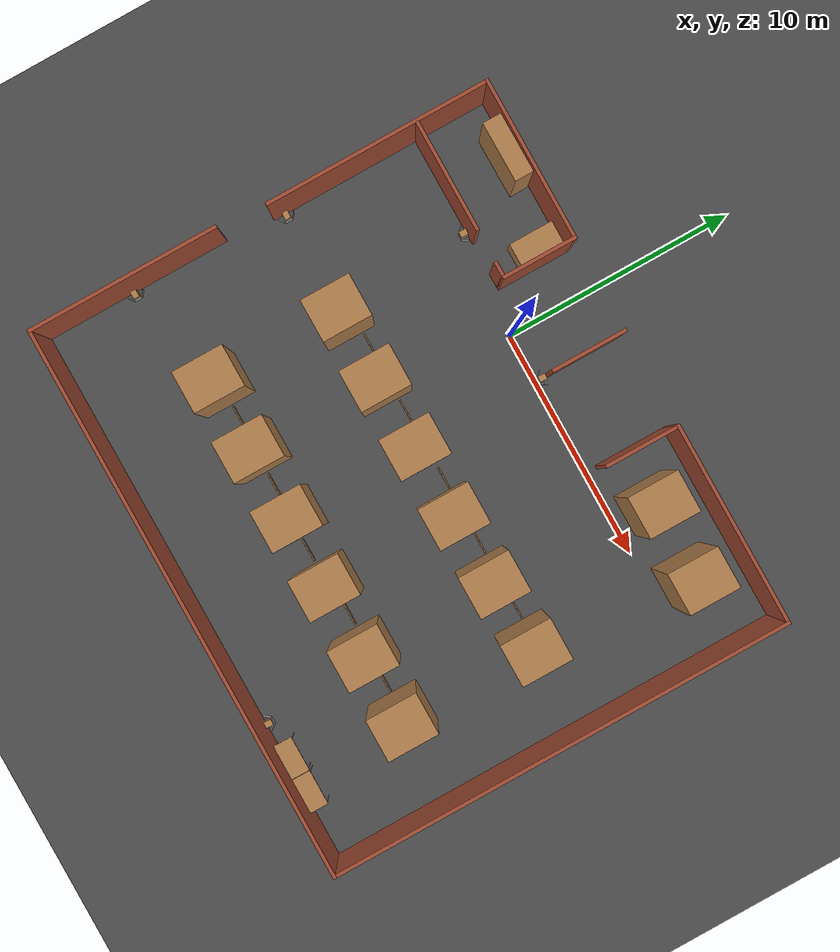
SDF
<sdf version="1.6">
 <world name="default">
  <light name="sun" type="directional">
   <pose>0 0 10 0 -0 0</pose>
   <diffuse>0.8 0.8 0.8 1</diffuse>
   <specular>0.2 0.2 0.2 1</specular>
   <attenuation>
    <range>1000</range>
    <constant>0.9</constant>
    <linear>0.01</linear>
    <quadratic>0.001</quadratic>
   </attenuation>
   <direction>-0.5 0.1 -0.9</direction>
  </light>
  <model name="ground_plane">
   <static>1</static>
   <link name="link">
    <collision name="collision">
     <geometry><plane><normal>0 0 1</normal><size>100 100</size></plane></geometry>
     <surface><friction><ode><mu>100</mu><mu2>50</mu2></ode></friction></surface>
    </collision>
    <visual name="visual">
     <cast_shadows>0</cast_shadows>
     <geometry><plane><normal>0 0 1</normal><size>100 100</size></plane></geometry>
     <material>
      <script><uri>file://media/materials/scripts/gazebo.material</uri><name>Gazebo/DarkGrey</name></script>
     </material>
    </visual>
   </link>
  </model>
  <gravity>0 0 -9.8</gravity>
  <magnetic_field>6e-06 2.3e-05 -4.2e-05</magnetic_field>
  <atmosphere type="adiabatic"/>
  <physics name="default_physics" default="0" type="ode">
   <max_step_size>0.001</max_step_size>
   <real_time_factor>1</real_time_factor>
   <real_time_update_rate>1000</real_time_update_rate>
  </physics>
  <scene><ambient>0.4 0.4 0.4 1</ambient><background>0.7 0.7 0.7 1</background><shadows>1</shadows></scene>
  <spherical_coordinates>
   <surface_model>EARTH_WGS84</surface_model>
   <latitude_deg>0</latitude_deg>
   <longitude_deg>0</longitude_deg>
   <elevation>0</elevation>
   <heading_deg>0</heading_deg>
  </spherical_coordinates>
  <model name="enviroment_1">
   <pose>2.98612 -6.2457 0 0 -0 0</pose>
   <link name="Wall_0">
    <collision name="Wall_0_Collision">
     <geometry><box><size>8.25 0.15 2.5</size></box></geometry>
     <pose>0 0 1.25 0 -0 0</pose>
    </collision>
    <visual name="Wall_0_Visual">
     <pose>0 0 1.25 0 -0 0</pose>
     <geometry><box><size>8.25 0.15 2.5</size></box></geometry>
     <material>
      <script><uri>file://media/materials/scripts/gazebo.material</uri><name>Gazebo/Bricks</name></script>
      <ambient>1 1 1 1</ambient>
     </material>
     <meta><layer>0</layer></meta>
    </visual>
    <pose>-11.925 -5.8997 0 0 -0 -1.5708</pose>
   </link>
   <link name="Wall_1">
    <collision name="Wall_1_Collision">
     <geometry><box><size>24 0.15 2.5</size></box></geometry>
     <pose>0 0 1.25 0 -0 0</pose>
    </collision>
    <visual name="Wall_1_Visual">
     <pose>0 0 1.25 0 -0 0</pose>
     <geometry><box><size>24 0.15 2.5</size></box></geometry>
     <material>
      <script><uri>file://media/materials/scripts/gazebo.material</uri><name>Gazebo/Bricks</name></script>
      <ambient>1 1 1 1</ambient>
     </material>
     <meta><layer>0</layer></meta>
    </visual>
    <pose>0 -9.9497 0 0 -0 0</pose>
   </link>
   <link name="Wall_11">
    <collision name="Wall_11_Collision">
     <geometry><box><size>3.25 0.15 2.5</size></box></geometry>
     <pose>0 0 1.25 0 -0 0</pose>
    </collision>
    <visual name="Wall_11_Visual">
     <pose>0 0 1.25 0 -0 0</pose>
     <geometry><box><size>3.25 0.15 2.5</size></box></geometry>
     <material>
      <script><uri>file://media/materials/scripts/gazebo.material</uri><name>Gazebo/Bricks</name></script>
      <ambient>1 1 1 1</ambient>
     </material>
     <meta><layer>0</layer></meta>
    </visual>
    <pose>-0.85303 8.33887 0 0 -0 1.5708</pose>
   </link>
   <link name="Wall_13">
    <collision name="Wall_13_Collision">
     <geometry><box><size>4.75 0.15 2.5</size></box></geometry>
     <pose>0 0 1.25 0 -0 0</pose>
    </collision>
    <visual name="Wall_13_Visual">
     <pose>0 0 1.25 0 -0 0</pose>
     <geometry><box><size>4.75 0.15 2.5</size></box></geometry>
     <material>
      <script><uri>file://media/materials/scripts/gazebo.material</uri><name>Gazebo/Bricks</name></script>
      <ambient>1 1 1 1</ambient>
     </material>
     <meta><layer>0</layer></meta>
    </visual>
    <pose>-9.29736 6.8497 0 0 -0 3.14159</pose>
   </link>
   <link name="Wall_2">
    <collision name="Wall_2_Collision">
     <geometry><box><size>20 0.15 2.5</size></box></geometry>
     <pose>0 0 1.25 0 -0 0</pose>
    </collision>
    <visual name="Wall_2_Visual">
     <pose>0 0 1.25 0 -0 0</pose>
     <geometry><box><size>20 0.15 2.5</size></box></geometry>
     <material>
      <script><uri>file://media/materials/scripts/gazebo.material</uri><name>Gazebo/Bricks</name></script>
      <ambient>1 1 1 1</ambient>
     </material>
     <meta><layer>0</layer></meta>
    </visual>
    <pose>11.925 -0.024702 0 0 -0 1.5708</pose>
   </link>
   <link name="Wall_3">
    <collision name="Wall_3_Collision">
     <geometry><box><size>8.75 0.15 2.5</size></box></geometry>
     <pose>0 0 1.25 0 -0 0</pose>
    </collision>
    <visual name="Wall_3_Visual">
     <pose>0 0 1.25 0 -0 0</pose>
     <geometry><box><size>8.75 0.15 2.5</size></box></geometry>
     <material>
      <script><uri>file://media/materials/scripts/gazebo.material</uri><name>Gazebo/Bricks</name></script>
      <ambient>1 1 1 1</ambient>
     </material>
     <meta><layer>0</layer></meta>
    </visual>
    <pose>7.625 9.9003 0 0 -0 3.14159</pose>
   </link>
   <link name="Wall_4">
    <collision name="Wall_4_Collision">
     <geometry><box><size>3.25 0.15 2.5</size></box></geometry>
     <pose>0 0 1.25 0 -0 0</pose>
    </collision>
    <visual name="Wall_4_Visual">
     <pose>0 0 1.25 0 -0 0</pose>
     <geometry><box><size>3.25 0.15 2.5</size></box></geometry>
     <material>
      <script><uri>file://media/materials/scripts/gazebo.material</uri><name>Gazebo/Bricks</name></script>
      <ambient>1 1 1 1</ambient>
     </material>
     <meta><layer>0</layer></meta>
    </visual>
    <pose>3.325 8.3503 0 0 -0 -1.5708</pose>
   </link>
   <link name="Wall_6">
    <collision name="Wall_6_Collision">
     <geometry><box><size>0.75 0.15 2.5</size></box></geometry>
     <pose>0 0 1.25 0 -0 0</pose>
    </collision>
    <visual name="Wall_6_Visual">
     <pose>0 0 1.25 0 -0 0</pose>
     <geometry><box><size>0.75 0.15 2.5</size></box></geometry>
     <material>
      <script><uri>file://media/materials/scripts/gazebo.material</uri><name>Gazebo/Bricks</name></script>
      <ambient>1 1 1 1</ambient>
     </material>
     <meta><layer>0</layer></meta>
    </visual>
    <pose>-5.17649 6.8497 0 0 -0 0</pose>
   </link>
   <link name="Wall_7">
    <collision name="Wall_7_Collision">
     <geometry><box><size>3.25 0.15 2.5</size></box></geometry>
     <pose>0 0 1.25 0 -0 0</pose>
    </collision>
    <visual name="Wall_7_Visual">
     <pose>0 0 1.25 0 -0 0</pose>
     <geometry><box><size>3.25 0.15 2.5</size></box></geometry>
     <material>
      <script><uri>file://media/materials/scripts/gazebo.material</uri><name>Gazebo/Bricks</name></script>
      <ambient>1 1 1 1</ambient>
     </material>
     <meta><layer>0</layer></meta>
    </visual>
    <pose>-4.87649 8.3997 0 0 -0 1.5708</pose>
   </link>
   <link name="Wall_8">
    <collision name="Wall_8_Collision">
     <geometry><box><size>7 0.15 2.5</size></box></geometry>
     <pose>0 0 1.25 0 -0 0</pose>
    </collision>
    <visual name="Wall_8_Visual">
     <pose>0 0 1.25 0 -0 0</pose>
     <geometry><box><size>7 0.15 2.5</size></box></geometry>
     <material>
      <script><uri>file://media/materials/scripts/gazebo.material</uri><name>Gazebo/Bricks</name></script>
      <ambient>1 1 1 1</ambient>
     </material>
     <meta><layer>0</layer></meta>
    </visual>
    <pose>-8.30149 9.9497 0 0 -0 3.14159</pose>
   </link>
   <link name="Wall_9">
    <collision name="Wall_9_Collision">
     <geometry><box><size>9.75 0.15 2.5</size></box></geometry>
     <pose>0 0 1.25 0 -0 0</pose>
    </collision>
    <visual name="Wall_9_Visual">
     <pose>0 0 1.25 0 -0 0</pose>
     <geometry><box><size>9.75 0.15 2.5</size></box></geometry>
     <material>
      <script><uri>file://media/materials/scripts/gazebo.material</uri><name>Gazebo/Bricks</name></script>
      <ambient>1 1 1 1</ambient>
     </material>
     <meta><layer>0</layer></meta>
    </visual>
    <pose>-11.7265 5.1497 0 0 -0 -1.5708</pose>
   </link>
   <static>1</static>
  </model>
  <model name="unit_box_clone">
   <pose>-0.889956 -5.56511 1.53205 1e-06 0 0.000132</pose>
   <link name="link">
    <inertial>
     <mass>1</mass>
     <inertia>
      <ixx>0.166667</ixx>
      <ixy>0</ixy>
      <ixz>0</ixz>
      <iyy>0.166667</iyy>
      <iyz>0</iyz>
      <izz>0.166667</izz>
     </inertia>
    </inertial>
    <collision name="collision"><geometry><box><size>1.78607 2.17889 3.06409</size></box></geometry></collision>
    <visual name="visual">
     <geometry><box><size>1.78607 2.17889 3.06409</size></box></geometry>
     <material>
      <script><name>Gazebo/Wood</name><uri>file://media/materials/scripts/gazebo.material</uri></script>
     </material>
    </visual>
   </link>
  </model>
  <model name="unit_box_clone_0">
   <pose>2.11215 -5.52237 1.53205 -1e-06 0 0.00019</pose>
   <link name="link">
    <inertial>
     <mass>1</mass>
     <inertia>
      <ixx>0.166667</ixx>
      <ixy>0</ixy>
      <ixz>0</ixz>
      <iyy>0.166667</iyy>
      <iyz>0</iyz>
      <izz>0.166667</izz>
     </inertia>
    </inertial>
    <collision name="collision"><geometry><box><size>1.78607 2.17889 3.06409</size></box></geometry></collision>
    <visual name="visual">
     <geometry><box><size>1.78607 2.17889 3.06409</size></box></geometry>
     <material>
      <script><name>Gazebo/Wood</name><uri>file://media/materials/scripts/gazebo.material</uri></script>
     </material>
    </visual>
   </link>
  </model>
  <model name="unit_box_clone_1">
   <pose>5.11301 -5.51097 1.53205 1e-06 -0 0.000162</pose>
   <link name="link">
    <inertial>
     <mass>1</mass>
     <inertia>
      <ixx>0.166667</ixx>
      <ixy>0</ixy>
      <ixz>0</ixz>
      <iyy>0.166667</iyy>
      <iyz>0</iyz>
      <izz>0.166667</izz>
     </inertia>
    </inertial>
    <collision name="collision"><geometry><box><size>1.78607 2.17889 3.06409</size></box></geometry></collision>
    <visual name="visual">
     <geometry><box><size>1.78607 2.17889 3.06409</size></box></geometry>
     <material>
      <script><name>Gazebo/Wood</name><uri>file://media/materials/scripts/gazebo.material</uri></script>
     </material>
    </visual>
   </link>
  </model>
  <model name="unit_box_clone_2">
   <pose>8.1033 -5.43309 1.53204 2e-06 -0 0.000123</pose>
   <link name="link">
    <inertial>
     <mass>1</mass>
     <inertia>
      <ixx>0.166667</ixx>
      <ixy>0</ixy>
      <ixz>0</ixz>
      <iyy>0.166667</iyy>
      <iyz>0</iyz>
      <izz>0.166667</izz>
     </inertia>
    </inertial>
    <collision name="collision"><geometry><box><size>1.78607 2.17889 3.06409</size></box></geometry></collision>
    <visual name="visual">
     <geometry><box><size>1.78607 2.17889 3.06409</size></box></geometry>
     <material>
      <script><name>Gazebo/Wood</name><uri>file://media/materials/scripts/gazebo.material</uri></script>
     </material>
    </visual>
   </link>
  </model>
  <model name="unit_box_clone_3">
   <pose>11.1034 -5.30341 1.53205 -1e-06 -0 0.00014</pose>
   <link name="link">
    <inertial>
     <mass>1</mass>
     <inertia>
      <ixx>0.166667</ixx>
      <ixy>0</ixy>
      <ixz>0</ixz>
      <iyy>0.166667</iyy>
      <iyz>0</iyz>
      <izz>0.166667</izz>
     </inertia>
    </inertial>
    <collision name="collision"><geometry><box><size>1.78607 2.17889 3.06409</size></box></geometry></collision>
    <visual name="visual">
     <geometry><box><size>1.78607 2.17889 3.06409</size></box></geometry>
     <material>
      <script><name>Gazebo/Wood</name><uri>file://media/materials/scripts/gazebo.material</uri></script>
     </material>
    </visual>
   </link>
  </model>
  <model name="unit_box_clone_4">
   <pose>8.58374 1.61175 1.53205 1e-06 0 0.000115</pose>
   <link name="link">
    <inertial>
     <mass>1</mass>
     <inertia>
      <ixx>0.166667</ixx>
      <ixy>0</ixy>
      <ixz>0</ixz>
      <iyy>0.166667</iyy>
      <iyz>0</iyz>
      <izz>0.166667</izz>
     </inertia>
    </inertial>
    <collision name="collision"><geometry><box><size>1.78607 2.17889 3.06409</size></box></geometry></collision>
    <visual name="visual">
     <geometry><box><size>1.78607 2.17889 3.06409</size></box></geometry>
     <material>
      <script><name>Gazebo/Wood</name><uri>file://media/materials/scripts/gazebo.material</uri></script>
     </material>
    </visual>
   </link>
  </model>
  <model name="unit_box_clone_5">
   <pose>11.8267 1.51636 1.53205 -1e-06 0 0.000151</pose>
   <link name="link">
    <inertial>
     <mass>1</mass>
     <inertia>
      <ixx>0.166667</ixx>
      <ixy>0</ixy>
      <ixz>0</ixz>
      <iyy>0.166667</iyy>
      <iyz>0</iyz>
      <izz>0.166667</izz>
     </inertia>
    </inertial>
    <collision name="collision"><geometry><box><size>1.78607 2.17889 3.06409</size></box></geometry></collision>
    <visual name="visual">
     <geometry><box><size>1.78607 2.17889 3.06409</size></box></geometry>
     <material>
      <script><name>Gazebo/Wood</name><uri>file://media/materials/scripts/gazebo.material</uri></script>
     </material>
    </visual>
   </link>
  </model>
  <model name="unit_box_clone_6">
   <pose>-3.9254 -11.0743 1.53204 -2e-06 -0 0.000138</pose>
   <link name="link">
    <inertial>
     <mass>1</mass>
     <inertia>
      <ixx>0.166667</ixx>
      <ixy>0</ixy>
      <ixz>0</ixz>
      <iyy>0.166667</iyy>
      <iyz>0</iyz>
      <izz>0.166667</izz>
     </inertia>
    </inertial>
    <collision name="collision"><geometry><box><size>1.78607 2.17889 3.06409</size></box></geometry></collision>
    <visual name="visual">
     <geometry><box><size>1.78607 2.17889 3.06409</size></box></geometry>
     <material>
      <script><name>Gazebo/Wood</name><uri>file://media/materials/scripts/gazebo.material</uri></script>
     </material>
    </visual>
   </link>
  </model>
  <model name="unit_box_clone_7">
   <pose>-0.889964 -11.0603 1.53205 -1e-06 0 0.000154</pose>
   <link name="link">
    <inertial>
     <mass>1</mass>
     <inertia>
      <ixx>0.166667</ixx>
      <ixy>0</ixy>
      <ixz>0</ixz>
      <iyy>0.166667</iyy>
      <iyz>0</iyz>
      <izz>0.166667</izz>
     </inertia>
    </inertial>
    <collision name="collision"><geometry><box><size>1.78607 2.17889 3.06409</size></box></geometry></collision>
    <visual name="visual">
     <geometry><box><size>1.78607 2.17889 3.06409</size></box></geometry>
     <material>
      <script><name>Gazebo/Wood</name><uri>file://media/materials/scripts/gazebo.material</uri></script>
     </material>
    </visual>
   </link>
  </model>
  <model name="unit_box_clone_8">
   <pose>2.11025 -11.0781 1.53205 1e-06 0 0.00015</pose>
   <link name="link">
    <inertial>
     <mass>1</mass>
     <inertia>
      <ixx>0.166667</ixx>
      <ixy>0</ixy>
      <ixz>0</ixz>
      <iyy>0.166667</iyy>
      <iyz>0</iyz>
      <izz>0.166667</izz>
     </inertia>
    </inertial>
    <collision name="collision"><geometry><box><size>1.78607 2.17889 3.06409</size></box></geometry></collision>
    <visual name="visual">
     <geometry><box><size>1.78607 2.17889 3.06409</size></box></geometry>
     <material>
      <script><name>Gazebo/Wood</name><uri>file://media/materials/scripts/gazebo.material</uri></script>
     </material>
    </visual>
   </link>
  </model>
  <model name="unit_box_clone_9">
   <pose>5.07629 -11.1138 1.53204 2e-06 -0 8.1e-05</pose>
   <link name="link">
    <inertial>
     <mass>1</mass>
     <inertia>
      <ixx>0.166667</ixx>
      <ixy>0</ixy>
      <ixz>0</ixz>
      <iyy>0.166667</iyy>
      <iyz>0</iyz>
      <izz>0.166667</izz>
     </inertia>
    </inertial>
    <collision name="collision"><geometry><box><size>1.78607 2.17889 3.06409</size></box></geometry></collision>
    <visual name="visual">
     <geometry><box><size>1.78607 2.17889 3.06409</size></box></geometry>
     <material>
      <script><name>Gazebo/Wood</name><uri>file://media/materials/scripts/gazebo.material</uri></script>
     </material>
    </visual>
   </link>
  </model>
  <model name="unit_box_clone_10">
   <pose>8.1123 -11.1173 1.53204 2e-06 -0 0.000136</pose>
   <link name="link">
    <inertial>
     <mass>1</mass>
     <inertia>
      <ixx>0.166667</ixx>
      <ixy>0</ixy>
      <ixz>0</ixz>
      <iyy>0.166667</iyy>
      <iyz>0</iyz>
      <izz>0.166667</izz>
     </inertia>
    </inertial>
    <collision name="collision"><geometry><box><size>1.78607 2.17889 3.06409</size></box></geometry></collision>
    <visual name="visual">
     <geometry><box><size>1.78607 2.17889 3.06409</size></box></geometry>
     <material>
      <script><name>Gazebo/Wood</name><uri>file://media/materials/scripts/gazebo.material</uri></script>
     </material>
    </visual>
   </link>
  </model>
  <model name="unit_box_clone_11">
   <pose>11.0953 -11.093 1.53205 -1e-06 0 0.000112</pose>
   <link name="link">
    <inertial>
     <mass>1</mass>
     <inertia>
      <ixx>0.166667</ixx>
      <ixy>0</ixy>
      <ixz>0</ixz>
      <iyy>0.166667</iyy>
      <iyz>0</iyz>
      <izz>0.166667</izz>
     </inertia>
    </inertial>
    <collision name="collision"><geometry><box><size>1.78607 2.17889 3.06409</size></box></geometry></collision>
    <visual name="visual">
     <geometry><box><size>1.78607 2.17889 3.06409</size></box></geometry>
     <material>
      <script><name>Gazebo/Wood</name><uri>file://media/materials/scripts/gazebo.material</uri></script>
     </material>
    </visual>
   </link>
  </model>
  <audio><device>default</device></audio>
  <model name="table">
   <static>1</static>
   <link name="link">
    <collision name="surface">
     <pose>0 0 1 0 -0 0</pose>
     <geometry><box><size>1.5 0.8 0.03</size></box></geometry>
     <surface><friction><ode><mu>0.6</mu><mu2>0.6</mu2></ode></friction></surface>
    </collision>
    <visual name="visual1">
     <pose>0 0 1 0 -0 0</pose>
     <geometry><box><size>1.5 0.8 0.03</size></box></geometry>
     <material>
      <script><uri>file://media/materials/scripts/gazebo.material</uri><name>Gazebo/Wood</name></script>
     </material>
    </visual>
    <collision name="front_left_leg">
     <pose>0.68 0.38 0.5 0 -0 0</pose>
     <geometry><cylinder><radius>0.02</radius><length>1</length></cylinder></geometry>
    </collision>
    <visual name="front_left_leg">
     <pose>0.68 0.38 0.5 0 -0 0</pose>
     <geometry><cylinder><radius>0.02</radius><length>1</length></cylinder></geometry>
     <material>
      <script><uri>file://media/materials/scripts/gazebo.material</uri><name>Gazebo/Grey</name></script>
     </material>
    </visual>
    <collision name="front_right_leg">
     <pose>0.68 -0.38 0.5 0 -0 0</pose>
     <geometry><cylinder><radius>0.02</radius><length>1</length></cylinder></geometry>
    </collision>
    <visual name="front_right_leg">
     <pose>0.68 -0.38 0.5 0 -0 0</pose>
     <geometry><cylinder><radius>0.02</radius><length>1</length></cylinder></geometry>
     <material>
      <script><uri>file://media/materials/scripts/gazebo.material</uri><name>Gazebo/Grey</name></script>
     </material>
    </visual>
    <collision name="back_right_leg">
     <pose>-0.68 -0.38 0.5 0 -0 0</pose>
     <geometry><cylinder><radius>0.02</radius><length>1</length></cylinder></geometry>
    </collision>
    <visual name="back_right_leg">
     <pose>-0.68 -0.38 0.5 0 -0 0</pose>
     <geometry><cylinder><radius>0.02</radius><length>1</length></cylinder></geometry>
     <material>
      <script><uri>file://media/materials/scripts/gazebo.material</uri><name>Gazebo/Grey</name></script>
     </material>
    </visual>
    <collision name="back_left_leg">
     <pose>-0.68 0.38 0.5 0 -0 0</pose>
     <geometry><cylinder><radius>0.02</radius><length>1</length></cylinder></geometry>
    </collision>
    <visual name="back_left_leg">
     <pose>-0.68 0.38 0.5 0 -0 0</pose>
     <geometry><cylinder><radius>0.02</radius><length>1</length></cylinder></geometry>
     <material>
      <script><uri>file://media/materials/scripts/gazebo.material</uri><name>Gazebo/Grey</name></script>
     </material>
    </visual>
   </link>
   <pose>10.3967 -15.7211 0 0 -0 0</pose>
  </model>
  <model name="table_0">
   <static>1</static>
   <link name="link">
    <collision name="surface">
     <pose>0 0 1 0 -0 0</pose>
     <geometry><box><size>1.5 0.8 0.03</size></box></geometry>
     <surface><friction><ode><mu>0.6</mu><mu2>0.6</mu2></ode></friction></surface>
    </collision>
    <visual name="visual1">
     <pose>0 0 1 0 -0 0</pose>
     <geometry><box><size>1.5 0.8 0.03</size></box></geometry>
     <material>
      <script><uri>file://media/materials/scripts/gazebo.material</uri><name>Gazebo/Wood</name></script>
     </material>
    </visual>
    <collision name="front_left_leg">
     <pose>0.68 0.38 0.5 0 -0 0</pose>
     <geometry><cylinder><radius>0.02</radius><length>1</length></cylinder></geometry>
    </collision>
    <visual name="front_left_leg">
     <pose>0.68 0.38 0.5 0 -0 0</pose>
     <geometry><cylinder><radius>0.02</radius><length>1</length></cylinder></geometry>
     <material>
      <script><uri>file://media/materials/scripts/gazebo.material</uri><name>Gazebo/Grey</name></script>
     </material>
    </visual>
    <collision name="front_right_leg">
     <pose>0.68 -0.38 0.5 0 -0 0</pose>
     <geometry><cylinder><radius>0.02</radius><length>1</length></cylinder></geometry>
    </collision>
    <visual name="front_right_leg">
     <pose>0.68 -0.38 0.5 0 -0 0</pose>
     <geometry><cylinder><radius>0.02</radius><length>1</length></cylinder></geometry>
     <material>
      <script><uri>file://media/materials/scripts/gazebo.material</uri><name>Gazebo/Grey</name></script>
     </material>
    </visual>
    <collision name="back_right_leg">
     <pose>-0.68 -0.38 0.5 0 -0 0</pose>
     <geometry><cylinder><radius>0.02</radius><length>1</length></cylinder></geometry>
    </collision>
    <visual name="back_right_leg">
     <pose>-0.68 -0.38 0.5 0 -0 0</pose>
     <geometry><cylinder><radius>0.02</radius><length>1</length></cylinder></geometry>
     <material>
      <script><uri>file://media/materials/scripts/gazebo.material</uri><name>Gazebo/Grey</name></script>
     </material>
    </visual>
    <collision name="back_left_leg">
     <pose>-0.68 0.38 0.5 0 -0 0</pose>
     <geometry><cylinder><radius>0.02</radius><length>1</length></cylinder></geometry>
    </collision>
    <visual name="back_left_leg">
     <pose>-0.68 0.38 0.5 0 -0 0</pose>
     <geometry><cylinder><radius>0.02</radius><length>1</length></cylinder></geometry>
     <material>
      <script><uri>file://media/materials/scripts/gazebo.material</uri><name>Gazebo/Grey</name></script>
     </material>
    </visual>
   </link>
   <pose>11.9134 -15.7244 0 0 -0 0</pose>
  </model>
  <model name="Aruco tag100">
   <static>1</static>
   <link name="robot_link">
    <visual name="body_visual">
     <geometry><box><size>0.3 0.3 0.02</size></box></geometry>
     <material>
      <script><uri>model://tag_100/materials/scripts/tag.material</uri><name>aruco_tag_100</name></script>
     </material>
    </visual>
   </link>
   <pose>2.13797 0.140124 0.2 1.57 -0 0</pose>
  </model>
  <model name="Aruco tag100_clone">
   <static>1</static>
   <link name="robot_link">
    <visual name="body_visual">
     <geometry><box><size>0.3 0.3 0.02</size></box></geometry>
     <material>
      <script><uri>model://tag_100/materials/scripts/tag.material</uri><name>aruco_tag_100</name></script>
     </material>
    </visual>
   </link>
   <pose>1.89484 0.266603 0.2 1.57028 -0.000603 -0.96</pose>
  </model>
  <model name="Aruco tag100_clone_clone">
   <static>1</static>
   <link name="robot_link">
    <visual name="body_visual">
     <geometry><box><size>0.3 0.3 0.02</size></box></geometry>
     <material>
      <script><uri>model://tag_100/materials/scripts/tag.material</uri><name>aruco_tag_100</name></script>
     </material>
    </visual>
   </link>
   <pose>2.38303 0.266773 0.2 1.57028 -0.000603 0.96</pose>
  </model>
  <model name="Support_box_wood_0">
   <link name="link">
    <inertial>
     <mass>0.0406949</mass>
     <inertia>
      <ixx>0.00114102</ixx>
      <ixy>0</ixy>
      <ixz>0</ixz>
      <iyy>0.00102768</iyy>
      <iyz>0</iyz>
      <izz>0.000581951</izz>
     </inertia>
    </inertial>
    <pose>0.062754 0.860403 -0.243846 0 -0 0</pose>
    <visual name="visual">
     <geometry><box><size>0.252854 0.320175 0.483682</size></box></geometry>
     <material>
      <script><name>Gazebo/Wood</name><uri>file://media/materials/scripts/gazebo.material</uri></script>
      <shader type="vertex"><normal_map>__default__</normal_map></shader>
      <ambient>0.3 0.3 0.3 1</ambient>
      <diffuse>0.7 0.7 0.7 1</diffuse>
      <specular>0.01 0.01 0.01 1</specular>
      <emissive>0 0 0 1</emissive>
     </material>
    </visual>
    <visual name="ModelPreview_4::link::visual_1">
     <geometry><box><size>0.252854 0.320175 0.483682</size></box></geometry>
     <material>
      <script><name>Gazebo/Wood</name><uri>file://media/materials/scripts/gazebo.material</uri></script>
      <shader type="vertex"><normal_map>__default__</normal_map></shader>
      <ambient>0.3 0.3 0.3 1</ambient>
      <diffuse>0.7 0.7 0.7 1</diffuse>
      <specular>0.01 0.01 0.01 1</specular>
      <emissive>0 0 0 1</emissive>
     </material>
    </visual>
    <collision name="collision">
     <geometry><box><size>0.262854 0.320175 0.483683</size></box></geometry>
     <surface>
      <friction>
       <ode><mu>1</mu><mu2>1</mu2><fdir1>0 0 0</fdir1><slip1>0</slip1><slip2>0</slip2></ode>
       <torsional>
        <coefficient>1</coefficient>
        <patch_radius>0</patch_radius>
        <surface_radius>0</surface_radius>
        <use_patch_radius>1</use_patch_radius>
        <ode><slip>0</slip></ode>
       </torsional>
      </friction>
      <bounce><restitution_coefficient>0</restitution_coefficient><threshold>1e+06</threshold></bounce>
      <contact>
       <collide_without_contact>0</collide_without_contact>
       <collide_without_contact_bitmask>1</collide_without_contact_bitmask>
       <collide_bitmask>1</collide_bitmask>
       <ode>
        <soft_cfm>0</soft_cfm>
        <soft_erp>0.2</soft_erp>
        <kp>1e+13</kp>
        <kd>1</kd>
        <max_vel>0.01</max_vel>
        <min_depth>0</min_depth>
       </ode>
       <bullet>
        <split_impulse>1</split_impulse>
        <split_impulse_penetration_threshold>-0.01</split_impulse_penetration_threshold>
        <soft_cfm>0</soft_cfm>
        <soft_erp>0.2</soft_erp>
        <kp>1e+13</kp>
        <kd>1</kd>
       </bullet>
      </contact>
     </surface>
    </collision>
   </link>
   <static>0</static>
   <pose>-4.49737 -0.49187 0.485697 -1.3e-05 0 0.002179</pose>
  </model>
  <model name="Support_box_wood">
   <link name="link">
    <inertial>
     <mass>0.0406949</mass>
     <inertia>
      <ixx>0.00114102</ixx>
      <ixy>0</ixy>
      <ixz>0</ixz>
      <iyy>0.00102768</iyy>
      <iyz>0</iyz>
      <izz>0.000581951</izz>
     </inertia>
    </inertial>
    <pose>0.062754 0.860403 -0.243846 0 -0 0</pose>
    <visual name="visual">
     <geometry><box><size>0.252854 0.320175 0.483682</size></box></geometry>
     <material>
      <script><name>Gazebo/Wood</name><uri>file://media/materials/scripts/gazebo.material</uri></script>
      <shader type="vertex"><normal_map>__default__</normal_map></shader>
      <ambient>0.3 0.3 0.3 1</ambient>
      <diffuse>0.7 0.7 0.7 1</diffuse>
      <specular>0.01 0.01 0.01 1</specular>
      <emissive>0 0 0 1</emissive>
     </material>
    </visual>
    <visual name="ModelPreview_4::link::visual_1">
     <geometry><box><size>0.252854 0.320175 0.483682</size></box></geometry>
     <material>
      <script><name>Gazebo/Wood</name><uri>file://media/materials/scripts/gazebo.material</uri></script>
      <shader type="vertex"><normal_map>__default__</normal_map></shader>
      <ambient>0.3 0.3 0.3 1</ambient>
      <diffuse>0.7 0.7 0.7 1</diffuse>
      <specular>0.01 0.01 0.01 1</specular>
      <emissive>0 0 0 1</emissive>
     </material>
    </visual>
    <collision name="collision">
     <geometry><box><size>0.262854 0.320175 0.483683</size></box></geometry>
     <surface>
      <friction>
       <ode><mu>1</mu><mu2>1</mu2><fdir1>0 0 0</fdir1><slip1>0</slip1><slip2>0</slip2></ode>
       <torsional>
        <coefficient>1</coefficient>
        <patch_radius>0</patch_radius>
        <surface_radius>0</surface_radius>
        <use_patch_radius>1</use_patch_radius>
        <ode><slip>0</slip></ode>
       </torsional>
      </friction>
      <bounce><restitution_coefficient>0</restitution_coefficient><threshold>1e+06</threshold></bounce>
      <contact>
       <collide_without_contact>0</collide_without_contact>
       <collide_without_contact_bitmask>1</collide_without_contact_bitmask>
       <collide_bitmask>1</collide_bitmask>
       <ode>
        <soft_cfm>0</soft_cfm>
        <soft_erp>0.2</soft_erp>
        <kp>1e+13</kp>
        <kd>1</kd>
        <max_vel>0.01</max_vel>
        <min_depth>0</min_depth>
       </ode>
       <bullet>
        <split_impulse>1</split_impulse>
        <split_impulse_penetration_threshold>-0.01</split_impulse_penetration_threshold>
        <soft_cfm>0</soft_cfm>
        <soft_erp>0.2</soft_erp>
        <kp>1e+13</kp>
        <kd>1</kd>
       </bullet>
      </contact>
     </surface>
    </collision>
   </link>
   <static>0</static>
   <pose>-7.6449 -5.50951 0.485687 0 -0 1.57065</pose>
  </model>
  <model name="Aruco tag200">
   <static>1</static>
   <link name="robot_link">
    <visual name="body_visual">
     <geometry><box><size>0.3 0.3 0.02</size></box></geometry>
     <material>
      <script><uri>model://tag_200/materials/scripts/tag.material</uri><name>aruco_tag_200</name></script>
     </material>
    </visual>
   </link>
   <pose>-8.33203 -5.45397 0.2 3.14159 1.57 3.14159</pose>
  </model>
  <model name="Aruco tag200_clone">
   <static>1</static>
   <link name="robot_link">
    <visual name="body_visual">
     <geometry><box><size>0.3 0.3 0.02</size></box></geometry>
     <material>
      <script><uri>model://tag_200/materials/scripts/tag.material</uri><name>aruco_tag_200</name></script>
     </material>
    </visual>
   </link>
   <pose>-8.4533 -5.20272 0.2 -3.14088 1.57 0.91071</pose>
  </model>
  <model name="Aruco tag200_clone_clone">
   <static>1</static>
   <link name="robot_link">
    <visual name="body_visual">
     <geometry><box><size>0.3 0.3 0.02</size></box></geometry>
     <material>
      <script><uri>model://tag_200/materials/scripts/tag.material</uri><name>aruco_tag_200</name></script>
     </material>
    </visual>
   </link>
   <pose>-8.45452 -5.70482 0.2 3.14124 1.57 -0.911069</pose>
  </model>
  <model name="Support_box_wood_clone">
   <link name="link">
    <inertial>
     <mass>0.0406949</mass>
     <inertia>
      <ixx>0.00114102</ixx>
      <ixy>0</ixy>
      <ixz>0</ixz>
      <iyy>0.00102768</iyy>
      <iyz>0</iyz>
      <izz>0.000581951</izz>
     </inertia>
    </inertial>
    <pose>0.062754 0.860403 -0.243846 0 -0 0</pose>
    <visual name="visual">
     <geometry><box><size>0.252854 0.320175 0.483682</size></box></geometry>
     <material>
      <script><name>Gazebo/Wood</name><uri>file://media/materials/scripts/gazebo.material</uri></script>
      <shader type="vertex"><normal_map>__default__</normal_map></shader>
      <ambient>0.3 0.3 0.3 1</ambient>
      <diffuse>0.7 0.7 0.7 1</diffuse>
      <specular>0.01 0.01 0.01 1</specular>
      <emissive>0 0 0 1</emissive>
     </material>
    </visual>
    <visual name="ModelPreview_4::link::visual_1">
     <geometry><box><size>0.252854 0.320175 0.483682</size></box></geometry>
     <material>
      <script><name>Gazebo/Wood</name><uri>file://media/materials/scripts/gazebo.material</uri></script>
      <shader type="vertex"><normal_map>__default__</normal_map></shader>
      <ambient>0.3 0.3 0.3 1</ambient>
      <diffuse>0.7 0.7 0.7 1</diffuse>
      <specular>0.01 0.01 0.01 1</specular>
      <emissive>0 0 0 1</emissive>
     </material>
    </visual>
    <collision name="collision">
     <geometry><box><size>0.262854 0.320175 0.483683</size></box></geometry>
     <surface>
      <friction>
       <ode><mu>1</mu><mu2>1</mu2><fdir1>0 0 0</fdir1><slip1>0</slip1><slip2>0</slip2></ode>
       <torsional>
        <coefficient>1</coefficient>
        <patch_radius>0</patch_radius>
        <surface_radius>0</surface_radius>
        <use_patch_radius>1</use_patch_radius>
        <ode><slip>0</slip></ode>
       </torsional>
      </friction>
      <bounce><restitution_coefficient>0</restitution_coefficient><threshold>1e+06</threshold></bounce>
      <contact>
       <collide_without_contact>0</collide_without_contact>
       <collide_without_contact_bitmask>1</collide_without_contact_bitmask>
       <collide_bitmask>1</collide_bitmask>
       <ode>
        <soft_cfm>0</soft_cfm>
        <soft_erp>0.2</soft_erp>
        <kp>1e+13</kp>
        <kd>1</kd>
        <max_vel>0.01</max_vel>
        <min_depth>0</min_depth>
       </ode>
       <bullet>
        <split_impulse>1</split_impulse>
        <split_impulse_penetration_threshold>-0.01</split_impulse_penetration_threshold>
        <soft_cfm>0</soft_cfm>
        <soft_erp>0.2</soft_erp>
        <kp>1e+13</kp>
        <kd>1</kd>
       </bullet>
      </contact>
     </surface>
    </collision>
   </link>
   <static>0</static>
   <pose>2.06843 -0.552281 0.485687 0 -0 4e-06</pose>
  </model>
  <model name="Aruco tag101">
   <static>1</static>
   <link name="robot_link">
    <visual name="body_visual">
     <geometry><box><size>0.3 0.3 0.02</size></box></geometry>
     <material>
      <script><uri>model://tag_101/materials/scripts/tag.material</uri><name>aruco_tag_101</name></script>
     </material>
    </visual>
   </link>
   <pose>-4.43997 0.20897 0.2 1.57 -0 0</pose>
  </model>
  <model name="Aruco tag101_clone">
   <static>1</static>
   <link name="robot_link">
    <visual name="body_visual">
     <geometry><box><size>0.3 0.3 0.02</size></box></geometry>
     <material>
      <script><uri>model://tag_101/materials/scripts/tag.material</uri><name>aruco_tag_101</name></script>
     </material>
    </visual>
   </link>
   <pose>-4.18968 0.331448 0.2 1.57 -0 0.909999</pose>
  </model>
  <model name="Aruco tag101_clone_clone">
   <static>1</static>
   <link name="robot_link">
    <visual name="body_visual">
     <geometry><box><size>0.3 0.3 0.02</size></box></geometry>
     <material>
      <script><uri>model://tag_101/materials/scripts/tag.material</uri><name>aruco_tag_101</name></script>
     </material>
    </visual>
   </link>
   <pose>-4.69039 0.331481 0.2 1.57 -0 -0.909999</pose>
  </model>
  <model name="Support_box_wood_clone_clone">
   <link name="link">
    <inertial>
     <mass>0.0406949</mass>
     <inertia>
      <ixx>0.00114102</ixx>
      <ixy>0</ixy>
      <ixz>0</ixz>
      <iyy>0.00102768</iyy>
      <iyz>0</iyz>
      <izz>0.000581951</izz>
     </inertia>
    </inertial>
    <pose>0.062754 0.860403 -0.243846 0 -0 0</pose>
    <visual name="visual">
     <geometry><box><size>0.252854 0.320175 0.483682</size></box></geometry>
     <material>
      <script><name>Gazebo/Wood</name><uri>file://media/materials/scripts/gazebo.material</uri></script>
      <shader type="vertex"><normal_map>__default__</normal_map></shader>
      <ambient>0.3 0.3 0.3 1</ambient>
      <diffuse>0.7 0.7 0.7 1</diffuse>
      <specular>0.01 0.01 0.01 1</specular>
      <emissive>0 0 0 1</emissive>
     </material>
    </visual>
    <visual name="ModelPreview_4::link::visual_1">
     <geometry><box><size>0.252854 0.320175 0.483682</size></box></geometry>
     <material>
      <script><name>Gazebo/Wood</name><uri>file://media/materials/scripts/gazebo.material</uri></script>
      <shader type="vertex"><normal_map>__default__</normal_map></shader>
      <ambient>0.3 0.3 0.3 1</ambient>
      <diffuse>0.7 0.7 0.7 1</diffuse>
      <specular>0.01 0.01 0.01 1</specular>
      <emissive>0 0 0 1</emissive>
     </material>
    </visual>
    <collision name="collision">
     <geometry><box><size>0.262854 0.320175 0.483683</size></box></geometry>
     <surface>
      <friction>
       <ode><mu>1</mu><mu2>1</mu2><fdir1>0 0 0</fdir1><slip1>0</slip1><slip2>0</slip2></ode>
       <torsional>
        <coefficient>1</coefficient>
        <patch_radius>0</patch_radius>
        <surface_radius>0</surface_radius>
        <use_patch_radius>1</use_patch_radius>
        <ode><slip>0</slip></ode>
       </torsional>
      </friction>
      <bounce><restitution_coefficient>0</restitution_coefficient><threshold>1e+06</threshold></bounce>
      <contact>
       <collide_without_contact>0</collide_without_contact>
       <collide_without_contact_bitmask>1</collide_without_contact_bitmask>
       <collide_bitmask>1</collide_bitmask>
       <ode>
        <soft_cfm>0</soft_cfm>
        <soft_erp>0.2</soft_erp>
        <kp>1e+13</kp>
        <kd>1</kd>
        <max_vel>0.01</max_vel>
        <min_depth>0</min_depth>
       </ode>
       <bullet>
        <split_impulse>1</split_impulse>
        <split_impulse_penetration_threshold>-0.01</split_impulse_penetration_threshold>
        <soft_cfm>0</soft_cfm>
        <soft_erp>0.2</soft_erp>
        <kp>1e+13</kp>
        <kd>1</kd>
       </bullet>
      </contact>
     </surface>
    </collision>
   </link>
   <static>0</static>
   <pose>8.77795 -16.8207 0.485673 1.4e-05 -0 0.000104</pose>
  </model>
  <model name="Aruco tag102">
   <static>1</static>
   <link name="robot_link">
    <visual name="body_visual">
     <geometry><box><size>0.3 0.3 0.02</size></box></geometry>
     <material>
      <script><uri>model://tag_102/materials/scripts/tag.material</uri><name>aruco_tag_102</name></script>
     </material>
    </visual>
   </link>
   <pose>8.84643 -15.7937 0.2 1.57 -0 0</pose>
  </model>
  <model name="Aruco tag102_clone">
   <static>1</static>
   <link name="robot_link">
    <visual name="body_visual">
     <geometry><box><size>0.3 0.3 0.02</size></box></geometry>
     <material>
      <script><uri>model://tag_102/materials/scripts/tag.material</uri><name>aruco_tag_102</name></script>
     </material>
    </visual>
   </link>
   <pose>8.59529 -15.9151 0.2 1.57 -0 0.909999</pose>
  </model>
  <model name="Aruco tag102_clone_clone">
   <static>1</static>
   <link name="robot_link">
    <visual name="body_visual">
     <geometry><box><size>0.3 0.3 0.02</size></box></geometry>
     <material>
      <script><uri>model://tag_102/materials/scripts/tag.material</uri><name>aruco_tag_102</name></script>
     </material>
    </visual>
   </link>
   <pose>9.09641 -15.916 0.2 1.57 -0 -0.909999</pose>
  </model>
  <model name="Support_box_wood_clone_0">
   <link name="link">
    <inertial>
     <mass>0.0406949</mass>
     <inertia>
      <ixx>0.00114102</ixx>
      <ixy>0</ixy>
      <ixz>0</ixz>
      <iyy>0.00102768</iyy>
      <iyz>0</iyz>
      <izz>0.000581951</izz>
     </inertia>
    </inertial>
    <pose>0.062754 0.860403 -0.243846 0 -0 0</pose>
    <visual name="visual">
     <geometry><box><size>0.252854 0.320175 0.483682</size></box></geometry>
     <material>
      <script><name>Gazebo/Wood</name><uri>file://media/materials/scripts/gazebo.material</uri></script>
      <shader type="vertex"><normal_map>__default__</normal_map></shader>
      <ambient>0.3 0.3 0.3 1</ambient>
      <diffuse>0.7 0.7 0.7 1</diffuse>
      <specular>0.01 0.01 0.01 1</specular>
      <emissive>0 0 0 1</emissive>
     </material>
    </visual>
    <visual name="ModelPreview_4::link::visual_1">
     <geometry><box><size>0.252854 0.320175 0.483682</size></box></geometry>
     <material>
      <script><name>Gazebo/Wood</name><uri>file://media/materials/scripts/gazebo.material</uri></script>
      <shader type="vertex"><normal_map>__default__</normal_map></shader>
      <ambient>0.3 0.3 0.3 1</ambient>
      <diffuse>0.7 0.7 0.7 1</diffuse>
      <specular>0.01 0.01 0.01 1</specular>
      <emissive>0 0 0 1</emissive>
     </material>
    </visual>
    <collision name="collision">
     <geometry><box><size>0.262854 0.320175 0.483683</size></box></geometry>
     <surface>
      <friction>
       <ode><mu>1</mu><mu2>1</mu2><fdir1>0 0 0</fdir1><slip1>0</slip1><slip2>0</slip2></ode>
       <torsional>
        <coefficient>1</coefficient>
        <patch_radius>0</patch_radius>
        <surface_radius>0</surface_radius>
        <use_patch_radius>1</use_patch_radius>
        <ode><slip>0</slip></ode>
       </torsional>
      </friction>
      <bounce><restitution_coefficient>0</restitution_coefficient><threshold>1e+06</threshold></bounce>
      <contact>
       <collide_without_contact>0</collide_without_contact>
       <collide_without_contact_bitmask>1</collide_without_contact_bitmask>
       <collide_bitmask>1</collide_bitmask>
       <ode>
        <soft_cfm>0</soft_cfm>
        <soft_erp>0.2</soft_erp>
        <kp>1e+13</kp>
        <kd>1</kd>
        <max_vel>0.01</max_vel>
        <min_depth>0</min_depth>
       </ode>
       <bullet>
        <split_impulse>1</split_impulse>
        <split_impulse_penetration_threshold>-0.01</split_impulse_penetration_threshold>
        <soft_cfm>0</soft_cfm>
        <soft_erp>0.2</soft_erp>
        <kp>1e+13</kp>
        <kd>1</kd>
       </bullet>
      </contact>
     </surface>
    </collision>
   </link>
   <static>0</static>
   <pose>-7.84329 -12.327 0.485687 0 -0 1.57129</pose>
  </model>
  <model name="Aruco tag103">
   <static>1</static>
   <link name="robot_link">
    <visual name="body_visual">
     <geometry><box><size>0.3 0.3 0.02</size></box></geometry>
     <material>
      <script><uri>model://tag_103/materials/scripts/tag.material</uri><name>aruco_tag_103</name></script>
     </material>
    </visual>
   </link>
   <pose>-8.5298 -12.2644 0.2 -5.1e-05 1.57 5.1e-05</pose>
  </model>
  <model name="Aruco tag103_clone">
   <static>1</static>
   <link name="robot_link">
    <visual name="body_visual">
     <geometry><box><size>0.3 0.3 0.02</size></box></geometry>
     <material>
      <script><uri>model://tag_103/materials/scripts/tag.material</uri><name>aruco_tag_103</name></script>
     </material>
    </visual>
   </link>
   <pose>-8.64959 -12.0145 0.2 -0.001656 1.57 0.909889</pose>
  </model>
  <model name="Aruco tag103_clone_clone">
   <static>1</static>
   <link name="robot_link">
    <visual name="body_visual">
     <geometry><box><size>0.3 0.3 0.02</size></box></geometry>
     <material>
      <script><uri>model://tag_103/materials/scripts/tag.material</uri><name>aruco_tag_103</name></script>
     </material>
    </visual>
   </link>
   <pose>-8.65279 -12.5152 0.2 -0.001545 1.57 -0.911442</pose>
  </model>
  <model name="unit_box_0">
   <link name="link">
    <inertial>
     <mass>206.513</mass>
     <inertia><ixx>115.69</ixx><ixy>0</ixy><ixz>0</ixz><iyy>216.208</iyy><iyz>0</iyz><izz>122.645</izz></inertia>
    </inertial>
    <pose>0 0.254021 0.771856 0 -0 0</pose>
    <visual name="visual">
     <geometry><box><size>2.54631 0.801811 2.46568</size></box></geometry>
     <material>
      <script><name>Gazebo/Wood</name><uri>file://media/materials/scripts/gazebo.material</uri></script>
     </material>
    </visual>
    <collision name="collision">
     <geometry><box><size>2.54631 0.801811 2.46568</size></box></geometry>
     <surface>
      <friction>
       <ode><mu>1</mu><mu2>1</mu2><fdir1>0 0 0</fdir1><slip1>0</slip1><slip2>0</slip2></ode>
       <torsional>
        <coefficient>1</coefficient>
        <patch_radius>0</patch_radius>
        <surface_radius>0</surface_radius>
        <use_patch_radius>1</use_patch_radius>
        <ode><slip>0</slip></ode>
       </torsional>
      </friction>
      <bounce><restitution_coefficient>0</restitution_coefficient><threshold>1e+06</threshold></bounce>
      <contact>
       <collide_without_contact>0</collide_without_contact>
       <collide_without_contact_bitmask>1</collide_without_contact_bitmask>
       <collide_bitmask>1</collide_bitmask>
       <ode>
        <soft_cfm>0</soft_cfm>
        <soft_erp>0.2</soft_erp>
        <kp>1e+13</kp>
        <kd>1</kd>
        <max_vel>0.01</max_vel>
        <min_depth>0</min_depth>
       </ode>
       <bullet>
        <split_impulse>1</split_impulse>
        <split_impulse_penetration_threshold>-0.01</split_impulse_penetration_threshold>
        <soft_cfm>0</soft_cfm>
        <soft_erp>0.2</soft_erp>
        <kp>1e+13</kp>
        <kd>1</kd>
       </bullet>
      </contact>
     </surface>
    </collision>
   </link>
   <static>0</static>
   <pose>-6.14285 2.9103 0.460984 1e-06 -0 0.005648</pose>
  </model>
  <model name="unit_box_1">
   <link name="link">
    <inertial>
     <mass>4.46992</mass>
     <inertia><ixx>1.7353</ixx><ixy>0</ixy><ixz>0</ixz><iyy>0.744987</iyy><iyz>0</iyz><izz>1.7353</izz></inertia>
    </inertial>
    <visual name="visual">
     <geometry><box><size>1 1.91274 1</size></box></geometry>
     <material>
      <script><name>Gazebo/Wood</name><uri>file://media/materials/scripts/gazebo.material</uri></script>
     </material>
    </visual>
    <collision name="collision">
     <geometry><box><size>1 1.91274 1</size></box></geometry>
     <surface>
      <friction>
       <ode><mu>1</mu><mu2>1</mu2><fdir1>0 0 0</fdir1><slip1>0</slip1><slip2>0</slip2></ode>
       <torsional>
        <coefficient>1</coefficient>
        <patch_radius>0</patch_radius>
        <surface_radius>0</surface_radius>
        <use_patch_radius>1</use_patch_radius>
        <ode><slip>0</slip></ode>
       </torsional>
      </friction>
      <bounce><restitution_coefficient>0</restitution_coefficient><threshold>1e+06</threshold></bounce>
      <contact>
       <collide_without_contact>0</collide_without_contact>
       <collide_without_contact_bitmask>1</collide_without_contact_bitmask>
       <collide_bitmask>1</collide_bitmask>
       <ode>
        <soft_cfm>0</soft_cfm>
        <soft_erp>0.2</soft_erp>
        <kp>1e+13</kp>
        <kd>1</kd>
        <max_vel>0.01</max_vel>
        <min_depth>0</min_depth>
       </ode>
       <bullet>
        <split_impulse>1</split_impulse>
        <split_impulse_penetration_threshold>-0.01</split_impulse_penetration_threshold>
        <soft_cfm>0</soft_cfm>
        <soft_erp>0.2</soft_erp>
        <kp>1e+13</kp>
        <kd>1</kd>
       </bullet>
      </contact>
     </surface>
    </collision>
   </link>
   <static>0</static>
   <pose>-2.58138 2.6093 0.5 0 -0 1e-06</pose>
  </model>
  <model name="unit_box">
   <link name="link">
    <inertial>
     <mass>1648.57</mass>
     <inertia><ixx>1879.79</ixx><ixy>0</ixy><ixz>0</ixz><iyy>1718.68</iyy><iyz>0</iyz><izz>1060.42</izz></inertia>
    </inertial>
    <pose>-0 -0 -1.39134 0 -0 0</pose>
    <visual name="visual">
     <geometry><box><size>1.80916 2.1085 3.03929</size></box></geometry>
     <material>
      <script><name>Gazebo/Wood</name><uri>file://media/materials/scripts/gazebo.material</uri></script>
     </material>
    </visual>
    <collision name="collision">
     <geometry><box><size>1.80916 2.1085 3.03929</size></box></geometry>
     <surface>
      <friction>
       <ode><mu>1</mu><mu2>1</mu2><fdir1>0 0 0</fdir1><slip1>0</slip1><slip2>0</slip2></ode>
       <torsional>
        <coefficient>1</coefficient>
        <patch_radius>0</patch_radius>
        <surface_radius>0</surface_radius>
        <use_patch_radius>1</use_patch_radius>
        <ode><slip>0</slip></ode>
       </torsional>
      </friction>
      <bounce><restitution_coefficient>0</restitution_coefficient><threshold>1e+06</threshold></bounce>
      <contact>
       <collide_without_contact>0</collide_without_contact>
       <collide_without_contact_bitmask>1</collide_without_contact_bitmask>
       <collide_bitmask>1</collide_bitmask>
       <ode>
        <soft_cfm>0</soft_cfm>
        <soft_erp>0.2</soft_erp>
        <kp>1e+13</kp>
        <kd>1</kd>
        <max_vel>0.01</max_vel>
        <min_depth>0</min_depth>
       </ode>
       <bullet>
        <split_impulse>1</split_impulse>
        <split_impulse_penetration_threshold>-0.01</split_impulse_penetration_threshold>
        <soft_cfm>0</soft_cfm>
        <soft_erp>0.2</soft_erp>
        <kp>1e+13</kp>
        <kd>1</kd>
       </bullet>
      </contact>
     </surface>
    </collision>
   </link>
   <static>0</static>
   <pose>-3.91562 -5.5599 2.91099 0 -0 0.000128</pose>
  </model>
  <model name="fence">
   <link name="link">
    <inertial>
     <mass>0.0236206</mass>
     <inertia>
      <ixx>0.00046005</ixx>
      <ixy>0</ixy>
      <ixz>0</ixz>
      <iyy>0.00242368</iyy>
      <iyz>0</iyz>
      <izz>0.00197313</izz>
     </inertia>
    </inertial>
    <pose>0.164119 -0.397459 0.001761 0 -0 0</pose>
    <visual name="visual">
     <geometry><box><size>1 0.049108 0.480943</size></box></geometry>
     <material>
      <script><name>Gazebo/Wood</name><uri>file://media/materials/scripts/gazebo.material</uri></script>
      <shader type="pixel"><normal_map>__default__</normal_map></shader>
      <ambient>1 1 1 1</ambient>
      <diffuse>1 1 1 1</diffuse>
      <specular>0.2 0.2 0.2 1</specular>
      <emissive>0 0 0 1</emissive>
     </material>
    </visual>
    <collision name="collision">
     <geometry><box><size>1 0.049108 0.480943</size></box></geometry>
     <surface>
      <friction>
       <ode><mu>1</mu><mu2>1</mu2><fdir1>0 0 0</fdir1><slip1>0</slip1><slip2>0</slip2></ode>
       <torsional>
        <coefficient>1</coefficient>
        <patch_radius>0</patch_radius>
        <surface_radius>0</surface_radius>
        <use_patch_radius>1</use_patch_radius>
        <ode><slip>0</slip></ode>
       </torsional>
      </friction>
      <bounce><restitution_coefficient>0</restitution_coefficient><threshold>1e+06</threshold></bounce>
      <contact>
       <collide_without_contact>0</collide_without_contact>
       <collide_without_contact_bitmask>1</collide_without_contact_bitmask>
       <collide_bitmask>1</collide_bitmask>
       <ode>
        <soft_cfm>0</soft_cfm>
        <soft_erp>0.2</soft_erp>
        <kp>1e+13</kp>
        <kd>1</kd>
        <max_vel>0.01</max_vel>
        <min_depth>0</min_depth>
       </ode>
       <bullet>
        <split_impulse>1</split_impulse>
        <split_impulse_penetration_threshold>-0.01</split_impulse_penetration_threshold>
        <soft_cfm>0</soft_cfm>
        <soft_erp>0.2</soft_erp>
        <kp>1e+13</kp>
        <kd>1</kd>
       </bullet>
      </contact>
     </surface>
    </collision>
   </link>
   <static>0</static>
   <pose>9.44598 -10.6972 0.238705 1e-06 -9e-06 0.004586</pose>
  </model>
  <model name="fence_clone">
   <link name="link">
    <inertial>
     <mass>0.0236206</mass>
     <inertia>
      <ixx>0.00046005</ixx>
      <ixy>0</ixy>
      <ixz>0</ixz>
      <iyy>0.00242368</iyy>
      <iyz>0</iyz>
      <izz>0.00197313</izz>
     </inertia>
    </inertial>
    <pose>0.164119 -0.397459 0.001761 0 -0 0</pose>
    <visual name="visual">
     <geometry><box><size>1 0.049108 0.480943</size></box></geometry>
     <material>
      <script><name>Gazebo/Wood</name><uri>file://media/materials/scripts/gazebo.material</uri></script>
      <shader type="pixel"><normal_map>__default__</normal_map></shader>
      <ambient>1 1 1 1</ambient>
      <diffuse>1 1 1 1</diffuse>
      <specular>0.2 0.2 0.2 1</specular>
      <emissive>0 0 0 1</emissive>
     </material>
    </visual>
    <collision name="collision">
     <geometry><box><size>1 0.049108 0.480943</size></box></geometry>
     <surface>
      <friction>
       <ode><mu>1</mu><mu2>1</mu2><fdir1>0 0 0</fdir1><slip1>0</slip1><slip2>0</slip2></ode>
       <torsional>
        <coefficient>1</coefficient>
        <patch_radius>0</patch_radius>
        <surface_radius>0</surface_radius>
        <use_patch_radius>1</use_patch_radius>
        <ode><slip>0</slip></ode>
       </torsional>
      </friction>
      <bounce><restitution_coefficient>0</restitution_coefficient><threshold>1e+06</threshold></bounce>
      <contact>
       <collide_without_contact>0</collide_without_contact>
       <collide_without_contact_bitmask>1</collide_without_contact_bitmask>
       <collide_bitmask>1</collide_bitmask>
       <ode>
        <soft_cfm>0</soft_cfm>
        <soft_erp>0.2</soft_erp>
        <kp>1e+13</kp>
        <kd>1</kd>
        <max_vel>0.01</max_vel>
        <min_depth>0</min_depth>
       </ode>
       <bullet>
        <split_impulse>1</split_impulse>
        <split_impulse_penetration_threshold>-0.01</split_impulse_penetration_threshold>
        <soft_cfm>0</soft_cfm>
        <soft_erp>0.2</soft_erp>
        <kp>1e+13</kp>
        <kd>1</kd>
       </bullet>
      </contact>
     </surface>
    </collision>
   </link>
   <static>0</static>
   <pose>6.4229 -10.6127 0.238704 -1e-06 -9e-06 -0.003075</pose>
  </model>
  <model name="fence_clone_0">
   <link name="link">
    <inertial>
     <mass>0.0236206</mass>
     <inertia>
      <ixx>0.00046005</ixx>
      <ixy>0</ixy>
      <ixz>0</ixz>
      <iyy>0.00242368</iyy>
      <iyz>0</iyz>
      <izz>0.00197313</izz>
     </inertia>
    </inertial>
    <pose>0.164119 -0.397459 0.001761 0 -0 0</pose>
    <visual name="visual">
     <geometry><box><size>1 0.049108 0.480943</size></box></geometry>
     <material>
      <script><name>Gazebo/Wood</name><uri>file://media/materials/scripts/gazebo.material</uri></script>
      <shader type="pixel"><normal_map>__default__</normal_map></shader>
      <ambient>1 1 1 1</ambient>
      <diffuse>1 1 1 1</diffuse>
      <specular>0.2 0.2 0.2 1</specular>
      <emissive>0 0 0 1</emissive>
     </material>
    </visual>
    <collision name="collision">
     <geometry><box><size>1 0.049108 0.480943</size></box></geometry>
     <surface>
      <friction>
       <ode><mu>1</mu><mu2>1</mu2><fdir1>0 0 0</fdir1><slip1>0</slip1><slip2>0</slip2></ode>
       <torsional>
        <coefficient>1</coefficient>
        <patch_radius>0</patch_radius>
        <surface_radius>0</surface_radius>
        <use_patch_radius>1</use_patch_radius>
        <ode><slip>0</slip></ode>
       </torsional>
      </friction>
      <bounce><restitution_coefficient>0</restitution_coefficient><threshold>1e+06</threshold></bounce>
      <contact>
       <collide_without_contact>0</collide_without_contact>
       <collide_without_contact_bitmask>1</collide_without_contact_bitmask>
       <collide_bitmask>1</collide_bitmask>
       <ode>
        <soft_cfm>0</soft_cfm>
        <soft_erp>0.2</soft_erp>
        <kp>1e+13</kp>
        <kd>1</kd>
        <max_vel>0.01</max_vel>
        <min_depth>0</min_depth>
       </ode>
       <bullet>
        <split_impulse>1</split_impulse>
        <split_impulse_penetration_threshold>-0.01</split_impulse_penetration_threshold>
        <soft_cfm>0</soft_cfm>
        <soft_erp>0.2</soft_erp>
        <kp>1e+13</kp>
        <kd>1</kd>
       </bullet>
      </contact>
     </surface>
    </collision>
   </link>
   <static>0</static>
   <pose>3.40826 -10.8072 0.238705 1e-06 -9e-06 0.004582</pose>
  </model>
  <model name="fence_clone_1">
   <link name="link">
    <inertial>
     <mass>0.0236206</mass>
     <inertia>
      <ixx>0.00046005</ixx>
      <ixy>0</ixy>
      <ixz>0</ixz>
      <iyy>0.00242368</iyy>
      <iyz>0</iyz>
      <izz>0.00197313</izz>
     </inertia>
    </inertial>
    <pose>0.164119 -0.397459 0.001761 0 -0 0</pose>
    <visual name="visual">
     <geometry><box><size>1 0.049108 0.480943</size></box></geometry>
     <material>
      <script><name>Gazebo/Wood</name><uri>file://media/materials/scripts/gazebo.material</uri></script>
      <shader type="pixel"><normal_map>__default__</normal_map></shader>
      <ambient>1 1 1 1</ambient>
      <diffuse>1 1 1 1</diffuse>
      <specular>0.2 0.2 0.2 1</specular>
      <emissive>0 0 0 1</emissive>
     </material>
    </visual>
    <collision name="collision">
     <geometry><box><size>1 0.049108 0.480943</size></box></geometry>
     <surface>
      <friction>
       <ode><mu>1</mu><mu2>1</mu2><fdir1>0 0 0</fdir1><slip1>0</slip1><slip2>0</slip2></ode>
       <torsional>
        <coefficient>1</coefficient>
        <patch_radius>0</patch_radius>
        <surface_radius>0</surface_radius>
        <use_patch_radius>1</use_patch_radius>
        <ode><slip>0</slip></ode>
       </torsional>
      </friction>
      <bounce><restitution_coefficient>0</restitution_coefficient><threshold>1e+06</threshold></bounce>
      <contact>
       <collide_without_contact>0</collide_without_contact>
       <collide_without_contact_bitmask>1</collide_without_contact_bitmask>
       <collide_bitmask>1</collide_bitmask>
       <ode>
        <soft_cfm>0</soft_cfm>
        <soft_erp>0.2</soft_erp>
        <kp>1e+13</kp>
        <kd>1</kd>
        <max_vel>0.01</max_vel>
        <min_depth>0</min_depth>
       </ode>
       <bullet>
        <split_impulse>1</split_impulse>
        <split_impulse_penetration_threshold>-0.01</split_impulse_penetration_threshold>
        <soft_cfm>0</soft_cfm>
        <soft_erp>0.2</soft_erp>
        <kp>1e+13</kp>
        <kd>1</kd>
       </bullet>
      </contact>
     </surface>
    </collision>
   </link>
   <static>0</static>
   <pose>0.428148 -10.7336 0.238705 1e-06 -9e-06 0.004582</pose>
  </model>
  <model name="fence_clone_2">
   <link name="link">
    <inertial>
     <mass>0.0236206</mass>
     <inertia>
      <ixx>0.00046005</ixx>
      <ixy>0</ixy>
      <ixz>0</ixz>
      <iyy>0.00242368</iyy>
      <iyz>0</iyz>
      <izz>0.00197313</izz>
     </inertia>
    </inertial>
    <pose>0.164119 -0.397459 0.001761 0 -0 0</pose>
    <visual name="visual">
     <geometry><box><size>1 0.049108 0.480943</size></box></geometry>
     <material>
      <script><name>Gazebo/Wood</name><uri>file://media/materials/scripts/gazebo.material</uri></script>
      <shader type="pixel"><normal_map>__default__</normal_map></shader>
      <ambient>1 1 1 1</ambient>
      <diffuse>1 1 1 1</diffuse>
      <specular>0.2 0.2 0.2 1</specular>
      <emissive>0 0 0 1</emissive>
     </material>
    </visual>
    <collision name="collision">
     <geometry><box><size>1 0.049108 0.480943</size></box></geometry>
     <surface>
      <friction>
       <ode><mu>1</mu><mu2>1</mu2><fdir1>0 0 0</fdir1><slip1>0</slip1><slip2>0</slip2></ode>
       <torsional>
        <coefficient>1</coefficient>
        <patch_radius>0</patch_radius>
        <surface_radius>0</surface_radius>
        <use_patch_radius>1</use_patch_radius>
        <ode><slip>0</slip></ode>
       </torsional>
      </friction>
      <bounce><restitution_coefficient>0</restitution_coefficient><threshold>1e+06</threshold></bounce>
      <contact>
       <collide_without_contact>0</collide_without_contact>
       <collide_without_contact_bitmask>1</collide_without_contact_bitmask>
       <collide_bitmask>1</collide_bitmask>
       <ode>
        <soft_cfm>0</soft_cfm>
        <soft_erp>0.2</soft_erp>
        <kp>1e+13</kp>
        <kd>1</kd>
        <max_vel>0.01</max_vel>
        <min_depth>0</min_depth>
       </ode>
       <bullet>
        <split_impulse>1</split_impulse>
        <split_impulse_penetration_threshold>-0.01</split_impulse_penetration_threshold>
        <soft_cfm>0</soft_cfm>
        <soft_erp>0.2</soft_erp>
        <kp>1e+13</kp>
        <kd>1</kd>
       </bullet>
      </contact>
     </surface>
    </collision>
   </link>
   <static>0</static>
   <pose>-2.57306 -10.6392 0.238708 1e-06 9e-06 -0.000526</pose>
  </model>
  <model name="fence_clone_3">
   <link name="link">
    <inertial>
     <mass>0.0236206</mass>
     <inertia>
      <ixx>0.00046005</ixx>
      <ixy>0</ixy>
      <ixz>0</ixz>
      <iyy>0.00242368</iyy>
      <iyz>0</iyz>
      <izz>0.00197313</izz>
     </inertia>
    </inertial>
    <pose>0.164119 -0.397459 0.001761 0 -0 0</pose>
    <visual name="visual">
     <geometry><box><size>1 0.049108 0.480943</size></box></geometry>
     <material>
      <script><name>Gazebo/Wood</name><uri>file://media/materials/scripts/gazebo.material</uri></script>
      <shader type="pixel"><normal_map>__default__</normal_map></shader>
      <ambient>1 1 1 1</ambient>
      <diffuse>1 1 1 1</diffuse>
      <specular>0.2 0.2 0.2 1</specular>
      <emissive>0 0 0 1</emissive>
     </material>
    </visual>
    <collision name="collision">
     <geometry><box><size>1 0.049108 0.480943</size></box></geometry>
     <surface>
      <friction>
       <ode><mu>1</mu><mu2>1</mu2><fdir1>0 0 0</fdir1><slip1>0</slip1><slip2>0</slip2></ode>
       <torsional>
        <coefficient>1</coefficient>
        <patch_radius>0</patch_radius>
        <surface_radius>0</surface_radius>
        <use_patch_radius>1</use_patch_radius>
        <ode><slip>0</slip></ode>
       </torsional>
      </friction>
      <bounce><restitution_coefficient>0</restitution_coefficient><threshold>1e+06</threshold></bounce>
      <contact>
       <collide_without_contact>0</collide_without_contact>
       <collide_without_contact_bitmask>1</collide_without_contact_bitmask>
       <collide_bitmask>1</collide_bitmask>
       <ode>
        <soft_cfm>0</soft_cfm>
        <soft_erp>0.2</soft_erp>
        <kp>1e+13</kp>
        <kd>1</kd>
        <max_vel>0.01</max_vel>
        <min_depth>0</min_depth>
       </ode>
       <bullet>
        <split_impulse>1</split_impulse>
        <split_impulse_penetration_threshold>-0.01</split_impulse_penetration_threshold>
        <soft_cfm>0</soft_cfm>
        <soft_erp>0.2</soft_erp>
        <kp>1e+13</kp>
        <kd>1</kd>
       </bullet>
      </contact>
     </surface>
    </collision>
   </link>
   <static>0</static>
   <pose>-2.53955 -4.65469 0.238705 1e-06 -9e-06 0.004581</pose>
  </model>
  <model name="fence_clone_4">
   <link name="link">
    <inertial>
     <mass>0.0236206</mass>
     <inertia>
      <ixx>0.00046005</ixx>
      <ixy>0</ixy>
      <ixz>0</ixz>
      <iyy>0.00242368</iyy>
      <iyz>0</iyz>
      <izz>0.00197313</izz>
     </inertia>
    </inertial>
    <pose>0.164119 -0.397459 0.001761 0 -0 0</pose>
    <visual name="visual">
     <geometry><box><size>1 0.049108 0.480943</size></box></geometry>
     <material>
      <script><name>Gazebo/Wood</name><uri>file://media/materials/scripts/gazebo.material</uri></script>
      <shader type="pixel"><normal_map>__default__</normal_map></shader>
      <ambient>1 1 1 1</ambient>
      <diffuse>1 1 1 1</diffuse>
      <specular>0.2 0.2 0.2 1</specular>
      <emissive>0 0 0 1</emissive>
     </material>
    </visual>
    <collision name="collision">
     <geometry><box><size>1 0.049108 0.480943</size></box></geometry>
     <surface>
      <friction>
       <ode><mu>1</mu><mu2>1</mu2><fdir1>0 0 0</fdir1><slip1>0</slip1><slip2>0</slip2></ode>
       <torsional>
        <coefficient>1</coefficient>
        <patch_radius>0</patch_radius>
        <surface_radius>0</surface_radius>
        <use_patch_radius>1</use_patch_radius>
        <ode><slip>0</slip></ode>
       </torsional>
      </friction>
      <bounce><restitution_coefficient>0</restitution_coefficient><threshold>1e+06</threshold></bounce>
      <contact>
       <collide_without_contact>0</collide_without_contact>
       <collide_without_contact_bitmask>1</collide_without_contact_bitmask>
       <collide_bitmask>1</collide_bitmask>
       <ode>
        <soft_cfm>0</soft_cfm>
        <soft_erp>0.2</soft_erp>
        <kp>1e+13</kp>
        <kd>1</kd>
        <max_vel>0.01</max_vel>
        <min_depth>0</min_depth>
       </ode>
       <bullet>
        <split_impulse>1</split_impulse>
        <split_impulse_penetration_threshold>-0.01</split_impulse_penetration_threshold>
        <soft_cfm>0</soft_cfm>
        <soft_erp>0.2</soft_erp>
        <kp>1e+13</kp>
        <kd>1</kd>
       </bullet>
      </contact>
     </surface>
    </collision>
   </link>
   <static>0</static>
   <pose>0.448219 -4.69234 0.238707 -1e-06 9e-06 0.00452</pose>
  </model>
  <model name="fence_clone_5">
   <link name="link">
    <inertial>
     <mass>0.0236206</mass>
     <inertia>
      <ixx>0.00046005</ixx>
      <ixy>0</ixy>
      <ixz>0</ixz>
      <iyy>0.00242368</iyy>
      <iyz>0</iyz>
      <izz>0.00197313</izz>
     </inertia>
    </inertial>
    <pose>0.164119 -0.397459 0.001761 0 -0 0</pose>
    <visual name="visual">
     <geometry><box><size>1 0.049108 0.480943</size></box></geometry>
     <material>
      <script><name>Gazebo/Wood</name><uri>file://media/materials/scripts/gazebo.material</uri></script>
      <shader type="pixel"><normal_map>__default__</normal_map></shader>
      <ambient>1 1 1 1</ambient>
      <diffuse>1 1 1 1</diffuse>
      <specular>0.2 0.2 0.2 1</specular>
      <emissive>0 0 0 1</emissive>
     </material>
    </visual>
    <collision name="collision">
     <geometry><box><size>1 0.049108 0.480943</size></box></geometry>
     <surface>
      <friction>
       <ode><mu>1</mu><mu2>1</mu2><fdir1>0 0 0</fdir1><slip1>0</slip1><slip2>0</slip2></ode>
       <torsional>
        <coefficient>1</coefficient>
        <patch_radius>0</patch_radius>
        <surface_radius>0</surface_radius>
        <use_patch_radius>1</use_patch_radius>
        <ode><slip>0</slip></ode>
       </torsional>
      </friction>
      <bounce><restitution_coefficient>0</restitution_coefficient><threshold>1e+06</threshold></bounce>
      <contact>
       <collide_without_contact>0</collide_without_contact>
       <collide_without_contact_bitmask>1</collide_without_contact_bitmask>
       <collide_bitmask>1</collide_bitmask>
       <ode>
        <soft_cfm>0</soft_cfm>
        <soft_erp>0.2</soft_erp>
        <kp>1e+13</kp>
        <kd>1</kd>
        <max_vel>0.01</max_vel>
        <min_depth>0</min_depth>
       </ode>
       <bullet>
        <split_impulse>1</split_impulse>
        <split_impulse_penetration_threshold>-0.01</split_impulse_penetration_threshold>
        <soft_cfm>0</soft_cfm>
        <soft_erp>0.2</soft_erp>
        <kp>1e+13</kp>
        <kd>1</kd>
       </bullet>
      </contact>
     </surface>
    </collision>
   </link>
   <static>0</static>
   <pose>3.50684 -4.67245 0.238705 1e-06 -9e-06 0.00435</pose>
  </model>
  <model name="fence_clone_6">
   <link name="link">
    <inertial>
     <mass>0.0236206</mass>
     <inertia>
      <ixx>0.00046005</ixx>
      <ixy>0</ixy>
      <ixz>0</ixz>
      <iyy>0.00242368</iyy>
      <iyz>0</iyz>
      <izz>0.00197313</izz>
     </inertia>
    </inertial>
    <pose>0.164119 -0.397459 0.001761 0 -0 0</pose>
    <visual name="visual">
     <geometry><box><size>1 0.049108 0.480943</size></box></geometry>
     <material>
      <script><name>Gazebo/Wood</name><uri>file://media/materials/scripts/gazebo.material</uri></script>
      <shader type="pixel"><normal_map>__default__</normal_map></shader>
      <ambient>1 1 1 1</ambient>
      <diffuse>1 1 1 1</diffuse>
      <specular>0.2 0.2 0.2 1</specular>
      <emissive>0 0 0 1</emissive>
     </material>
    </visual>
    <collision name="collision">
     <geometry><box><size>1 0.049108 0.480943</size></box></geometry>
     <surface>
      <friction>
       <ode><mu>1</mu><mu2>1</mu2><fdir1>0 0 0</fdir1><slip1>0</slip1><slip2>0</slip2></ode>
       <torsional>
        <coefficient>1</coefficient>
        <patch_radius>0</patch_radius>
        <surface_radius>0</surface_radius>
        <use_patch_radius>1</use_patch_radius>
        <ode><slip>0</slip></ode>
       </torsional>
      </friction>
      <bounce><restitution_coefficient>0</restitution_coefficient><threshold>1e+06</threshold></bounce>
      <contact>
       <collide_without_contact>0</collide_without_contact>
       <collide_without_contact_bitmask>1</collide_without_contact_bitmask>
       <collide_bitmask>1</collide_bitmask>
       <ode>
        <soft_cfm>0</soft_cfm>
        <soft_erp>0.2</soft_erp>
        <kp>1e+13</kp>
        <kd>1</kd>
        <max_vel>0.01</max_vel>
        <min_depth>0</min_depth>
       </ode>
       <bullet>
        <split_impulse>1</split_impulse>
        <split_impulse_penetration_threshold>-0.01</split_impulse_penetration_threshold>
        <soft_cfm>0</soft_cfm>
        <soft_erp>0.2</soft_erp>
        <kp>1e+13</kp>
        <kd>1</kd>
       </bullet>
      </contact>
     </surface>
    </collision>
   </link>
   <static>0</static>
   <pose>6.45155 -4.6812 0.238704 -1e-06 -9e-06 0.002497</pose>
  </model>
  <model name="fence_clone_7">
   <link name="link">
    <inertial>
     <mass>0.0236206</mass>
     <inertia>
      <ixx>0.00046005</ixx>
      <ixy>0</ixy>
      <ixz>0</ixz>
      <iyy>0.00242368</iyy>
      <iyz>0</iyz>
      <izz>0.00197313</izz>
     </inertia>
    </inertial>
    <pose>0.164119 -0.397459 0.001761 0 -0 0</pose>
    <visual name="visual">
     <geometry><box><size>1 0.049108 0.480943</size></box></geometry>
     <material>
      <script><name>Gazebo/Wood</name><uri>file://media/materials/scripts/gazebo.material</uri></script>
      <shader type="pixel"><normal_map>__default__</normal_map></shader>
      <ambient>1 1 1 1</ambient>
      <diffuse>1 1 1 1</diffuse>
      <specular>0.2 0.2 0.2 1</specular>
      <emissive>0 0 0 1</emissive>
     </material>
    </visual>
    <collision name="collision">
     <geometry><box><size>1 0.049108 0.480943</size></box></geometry>
     <surface>
      <friction>
       <ode><mu>1</mu><mu2>1</mu2><fdir1>0 0 0</fdir1><slip1>0</slip1><slip2>0</slip2></ode>
       <torsional>
        <coefficient>1</coefficient>
        <patch_radius>0</patch_radius>
        <surface_radius>0</surface_radius>
        <use_patch_radius>1</use_patch_radius>
        <ode><slip>0</slip></ode>
       </torsional>
      </friction>
      <bounce><restitution_coefficient>0</restitution_coefficient><threshold>1e+06</threshold></bounce>
      <contact>
       <collide_without_contact>0</collide_without_contact>
       <collide_without_contact_bitmask>1</collide_without_contact_bitmask>
       <collide_bitmask>1</collide_bitmask>
       <ode>
        <soft_cfm>0</soft_cfm>
        <soft_erp>0.2</soft_erp>
        <kp>1e+13</kp>
        <kd>1</kd>
        <max_vel>0.01</max_vel>
        <min_depth>0</min_depth>
       </ode>
       <bullet>
        <split_impulse>1</split_impulse>
        <split_impulse_penetration_threshold>-0.01</split_impulse_penetration_threshold>
        <soft_cfm>0</soft_cfm>
        <soft_erp>0.2</soft_erp>
        <kp>1e+13</kp>
        <kd>1</kd>
       </bullet>
      </contact>
     </surface>
    </collision>
   </link>
   <static>0</static>
   <pose>9.43757 -4.67857 0.238704 1e-06 -1e-05 0.004358</pose>
  </model>
 </world>
</sdf>
